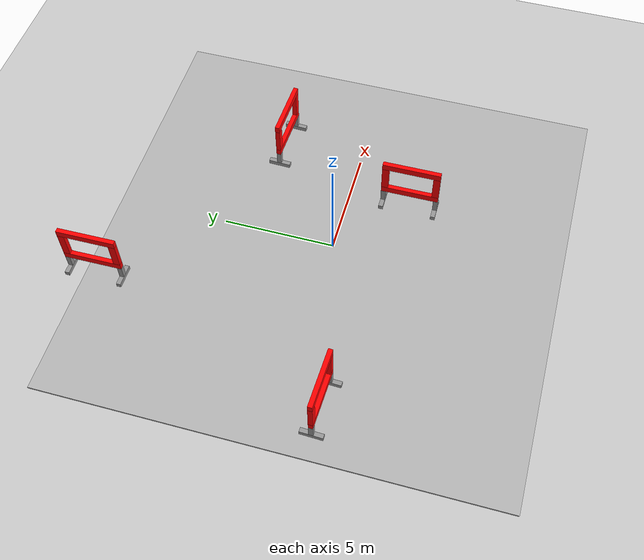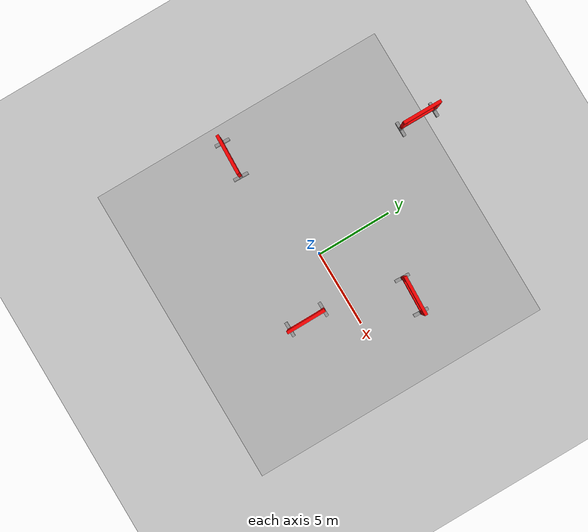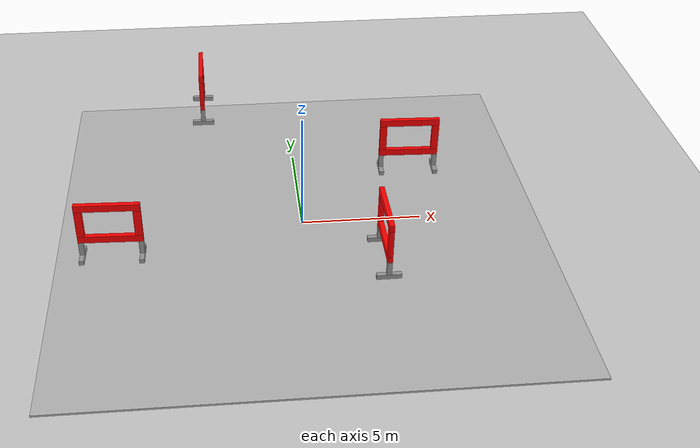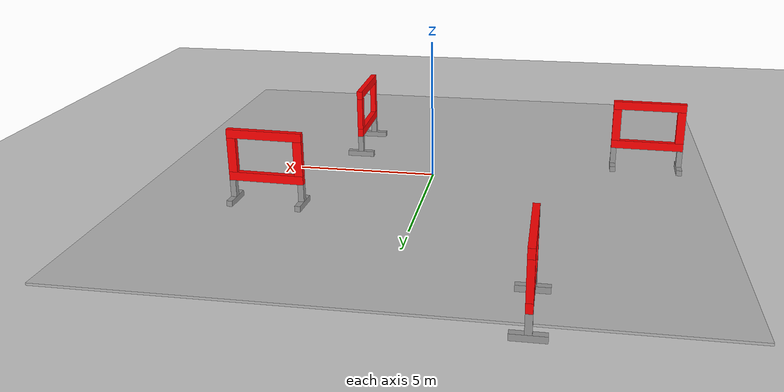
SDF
<sdf version="1.6">
 <world name="default">
  <light name="sun" type="directional">
   <pose>0 0 10 0 -0 0</pose>
   <diffuse>0.8 0.8 0.8 1</diffuse>
   <specular>0.2 0.2 0.2 1</specular>
   <attenuation>
    <range>1000</range>
    <constant>0.9</constant>
    <linear>0.01</linear>
    <quadratic>0.001</quadratic>
   </attenuation>
   <direction>-0.5 0.1 -0.9</direction>
  </light>
  <model name="ground_plane">
   <static>1</static>
   <link name="link">
    <collision name="collision">
     <geometry><plane><normal>0 0 1</normal><size>100 100</size></plane></geometry>
     <surface>
      <contact><collide_bitmask>65535</collide_bitmask></contact>
      <friction><ode><mu>100</mu><mu2>50</mu2></ode></friction>
     </surface>
    </collision>
    <visual name="visual">
     <cast_shadows>0</cast_shadows>
     <geometry><plane><normal>0 0 1</normal><size>100 100</size></plane></geometry>
     <material>
      <script><uri>file://media/materials/scripts/gazebo.material</uri><name>Gazebo/Grey</name></script>
     </material>
    </visual>
   </link>
  </model>
  <gravity>0 0 -9.8</gravity>
  <magnetic_field>6e-06 2.3e-05 -4.2e-05</magnetic_field>
  <atmosphere type="adiabatic"/>
  <physics name="default_physics" default="0" type="ode">
   <max_step_size>0.004</max_step_size>
   <real_time_factor>1</real_time_factor>
   <real_time_update_rate>250</real_time_update_rate>
  </physics>
  <scene><ambient>0.4 0.4 0.4 1</ambient><background>0.7 0.7 0.7 1</background><shadows>1</shadows></scene>
  <spherical_coordinates>
   <surface_model>EARTH_WGS84</surface_model>
   <latitude_deg>0</latitude_deg>
   <longitude_deg>0</longitude_deg>
   <elevation>0</elevation>
   <heading_deg>0</heading_deg>
  </spherical_coordinates>
  <model name="door_2_1.2_0">
   <model name="door">
    <link name="link_0">
     <inertial>
      <mass>1</mass>
      <inertia>
       <ixx>0.166667</ixx>
       <ixy>0</ixy>
       <ixz>0</ixz>
       <iyy>0.166667</iyy>
       <iyz>0</iyz>
       <izz>0.166667</izz>
      </inertia>
     </inertial>
     <pose>-0.195931 0.139969 -0.0875 0 -0 0</pose>
     <visual name="visual">
      <geometry><box><size>0.2 1 0.2</size></box></geometry>
      <material>
       <lighting>1</lighting>
       <script><uri>file://media/materials/scripts/gazebo.material</uri><name>Gazebo/Grey</name></script>
       <shader type="pixel"><normal_map>__default__</normal_map></shader>
       <ambient>0.4 0.4 0.4 1</ambient>
       <diffuse>0.7 0.7 0.7 1</diffuse>
       <specular>0.01 0.01 0.01 1</specular>
       <emissive>0 0 0 1</emissive>
      </material>
     </visual>
     <collision name="collision">
      <geometry><box><size>0.2 1 0.2</size></box></geometry>
      <surface>
       <friction>
        <ode><mu>1</mu><mu2>1</mu2><fdir1>0 0 0</fdir1><slip1>0</slip1><slip2>0</slip2></ode>
        <torsional>
         <coefficient>1</coefficient>
         <patch_radius>0</patch_radius>
         <surface_radius>0</surface_radius>
         <use_patch_radius>1</use_patch_radius>
         <ode><slip>0</slip></ode>
        </torsional>
       </friction>
       <bounce><restitution_coefficient>0</restitution_coefficient><threshold>1e+06</threshold></bounce>
       <contact>
        <collide_without_contact>0</collide_without_contact>
        <collide_without_contact_bitmask>1</collide_without_contact_bitmask>
        <collide_bitmask>1</collide_bitmask>
        <ode>
         <soft_cfm>0</soft_cfm>
         <soft_erp>0.2</soft_erp>
         <kp>1e+13</kp>
         <kd>1</kd>
         <max_vel>0.01</max_vel>
         <min_depth>0</min_depth>
        </ode>
        <bullet>
         <split_impulse>1</split_impulse>
         <split_impulse_penetration_threshold>-0.01</split_impulse_penetration_threshold>
         <soft_cfm>0</soft_cfm>
         <soft_erp>0.2</soft_erp>
         <kp>1e+13</kp>
         <kd>1</kd>
        </bullet>
       </contact>
      </surface>
     </collision>
    </link>
    <link name="link_0_clone">
     <inertial>
      <mass>1</mass>
      <inertia>
       <ixx>0.166667</ixx>
       <ixy>0</ixy>
       <ixz>0</ixz>
       <iyy>0.166667</iyy>
       <iyz>0</iyz>
       <izz>0.166667</izz>
      </inertia>
     </inertial>
     <pose>2.20407 0.139969 -0.0875 0 -0 0</pose>
     <visual name="visual">
      <geometry><box><size>0.2 1 0.2</size></box></geometry>
      <material>
       <lighting>1</lighting>
       <script><uri>file://media/materials/scripts/gazebo.material</uri><name>Gazebo/Grey</name></script>
       <shader type="pixel"><normal_map>__default__</normal_map></shader>
       <ambient>0.4 0.4 0.4 1</ambient>
       <diffuse>0.7 0.7 0.7 1</diffuse>
       <specular>0.01 0.01 0.01 1</specular>
       <emissive>0 0 0 1</emissive>
      </material>
     </visual>
     <collision name="collision">
      <geometry><box><size>0.2 1 0.2</size></box></geometry>
      <surface>
       <friction>
        <ode><mu>1</mu><mu2>1</mu2><fdir1>0 0 0</fdir1><slip1>0</slip1><slip2>0</slip2></ode>
        <torsional>
         <coefficient>1</coefficient>
         <patch_radius>0</patch_radius>
         <surface_radius>0</surface_radius>
         <use_patch_radius>1</use_patch_radius>
         <ode><slip>0</slip></ode>
        </torsional>
       </friction>
       <bounce><restitution_coefficient>0</restitution_coefficient><threshold>1e+06</threshold></bounce>
       <contact>
        <collide_without_contact>0</collide_without_contact>
        <collide_without_contact_bitmask>1</collide_without_contact_bitmask>
        <collide_bitmask>1</collide_bitmask>
        <ode>
         <soft_cfm>0</soft_cfm>
         <soft_erp>0.2</soft_erp>
         <kp>1e+13</kp>
         <kd>1</kd>
         <max_vel>0.01</max_vel>
         <min_depth>0</min_depth>
        </ode>
        <bullet>
         <split_impulse>1</split_impulse>
         <split_impulse_penetration_threshold>-0.01</split_impulse_penetration_threshold>
         <soft_cfm>0</soft_cfm>
         <soft_erp>0.2</soft_erp>
         <kp>1e+13</kp>
         <kd>1</kd>
        </bullet>
       </contact>
      </surface>
     </collision>
    </link>
    <link name="link_1">
     <inertial>
      <mass>1</mass>
      <inertia>
       <ixx>0.166667</ixx>
       <ixy>0</ixy>
       <ixz>0</ixz>
       <iyy>0.166667</iyy>
       <iyz>0</iyz>
       <izz>0.166667</izz>
      </inertia>
     </inertial>
     <pose>-0.195931 0.139969 0.3125 0 -0 0</pose>
     <visual name="visual">
      <geometry><box><size>0.2 0.2 0.6</size></box></geometry>
      <material>
       <lighting>1</lighting>
       <script><uri>file://media/materials/scripts/gazebo.material</uri><name>Gazebo/Grey</name></script>
       <shader type="pixel"><normal_map>__default__</normal_map></shader>
       <ambient>0.4 0.4 0.4 1</ambient>
       <diffuse>0.7 0.7 0.7 1</diffuse>
       <specular>0.01 0.01 0.01 1</specular>
       <emissive>0 0 0 1</emissive>
      </material>
     </visual>
     <collision name="collision">
      <geometry><box><size>0.2 0.2 0.6</size></box></geometry>
      <surface>
       <friction>
        <ode><mu>1</mu><mu2>1</mu2><fdir1>0 0 0</fdir1><slip1>0</slip1><slip2>0</slip2></ode>
        <torsional>
         <coefficient>1</coefficient>
         <patch_radius>0</patch_radius>
         <surface_radius>0</surface_radius>
         <use_patch_radius>1</use_patch_radius>
         <ode><slip>0</slip></ode>
        </torsional>
       </friction>
       <bounce><restitution_coefficient>0</restitution_coefficient><threshold>1e+06</threshold></bounce>
       <contact>
        <collide_without_contact>0</collide_without_contact>
        <collide_without_contact_bitmask>1</collide_without_contact_bitmask>
        <collide_bitmask>1</collide_bitmask>
        <ode>
         <soft_cfm>0</soft_cfm>
         <soft_erp>0.2</soft_erp>
         <kp>1e+13</kp>
         <kd>1</kd>
         <max_vel>0.01</max_vel>
         <min_depth>0</min_depth>
        </ode>
        <bullet>
         <split_impulse>1</split_impulse>
         <split_impulse_penetration_threshold>-0.01</split_impulse_penetration_threshold>
         <soft_cfm>0</soft_cfm>
         <soft_erp>0.2</soft_erp>
         <kp>1e+13</kp>
         <kd>1</kd>
        </bullet>
       </contact>
      </surface>
     </collision>
    </link>
    <link name="link_1_clone">
     <inertial>
      <mass>1</mass>
      <inertia>
       <ixx>0.166667</ixx>
       <ixy>0</ixy>
       <ixz>0</ixz>
       <iyy>0.166667</iyy>
       <iyz>0</iyz>
       <izz>0.166667</izz>
      </inertia>
     </inertial>
     <pose>2.20407 0.139969 0.3125 0 -0 0</pose>
     <visual name="visual">
      <geometry><box><size>0.2 0.2 0.6</size></box></geometry>
      <material>
       <lighting>1</lighting>
       <script><uri>file://media/materials/scripts/gazebo.material</uri><name>Gazebo/Grey</name></script>
       <shader type="pixel"><normal_map>__default__</normal_map></shader>
       <ambient>0.4 0.4 0.4 1</ambient>
       <diffuse>0.7 0.7 0.7 1</diffuse>
       <specular>0.01 0.01 0.01 1</specular>
       <emissive>0 0 0 1</emissive>
      </material>
     </visual>
     <collision name="collision">
      <geometry><box><size>0.2 0.2 0.6</size></box></geometry>
      <surface>
       <friction>
        <ode><mu>1</mu><mu2>1</mu2><fdir1>0 0 0</fdir1><slip1>0</slip1><slip2>0</slip2></ode>
        <torsional>
         <coefficient>1</coefficient>
         <patch_radius>0</patch_radius>
         <surface_radius>0</surface_radius>
         <use_patch_radius>1</use_patch_radius>
         <ode><slip>0</slip></ode>
        </torsional>
       </friction>
       <bounce><restitution_coefficient>0</restitution_coefficient><threshold>1e+06</threshold></bounce>
       <contact>
        <collide_without_contact>0</collide_without_contact>
        <collide_without_contact_bitmask>1</collide_without_contact_bitmask>
        <collide_bitmask>1</collide_bitmask>
        <ode>
         <soft_cfm>0</soft_cfm>
         <soft_erp>0.2</soft_erp>
         <kp>1e+13</kp>
         <kd>1</kd>
         <max_vel>0.01</max_vel>
         <min_depth>0</min_depth>
        </ode>
        <bullet>
         <split_impulse>1</split_impulse>
         <split_impulse_penetration_threshold>-0.01</split_impulse_penetration_threshold>
         <soft_cfm>0</soft_cfm>
         <soft_erp>0.2</soft_erp>
         <kp>1e+13</kp>
         <kd>1</kd>
        </bullet>
       </contact>
      </surface>
     </collision>
    </link>
    <link name="link_2">
     <inertial>
      <mass>1</mass>
      <inertia>
       <ixx>0.166667</ixx>
       <ixy>0</ixy>
       <ixz>0</ixz>
       <iyy>0.166667</iyy>
       <iyz>0</iyz>
       <izz>0.166667</izz>
      </inertia>
     </inertial>
     <pose>1.00407 0.139969 0.7625 0 -0 0</pose>
     <visual name="visual">
      <geometry><box><size>2.6 0.2 0.3</size></box></geometry>
      <material>
       <lighting>1</lighting>
       <script><uri>file://media/materials/scripts/gazebo.material</uri><name>Gazebo/Grey</name></script>
       <shader type="pixel"><normal_map>__default__</normal_map></shader>
       <ambient>1 0 0 1</ambient>
       <diffuse>0.7 0.7 0.7 1</diffuse>
       <specular>0.01 0.01 0.01 1</specular>
       <emissive>0 0 0 1</emissive>
      </material>
     </visual>
     <collision name="collision">
      <geometry><box><size>2.6 0.2 0.3</size></box></geometry>
      <surface>
       <friction>
        <ode><mu>1</mu><mu2>1</mu2><fdir1>0 0 0</fdir1><slip1>0</slip1><slip2>0</slip2></ode>
        <torsional>
         <coefficient>1</coefficient>
         <patch_radius>0</patch_radius>
         <surface_radius>0</surface_radius>
         <use_patch_radius>1</use_patch_radius>
         <ode><slip>0</slip></ode>
        </torsional>
       </friction>
       <bounce><restitution_coefficient>0</restitution_coefficient><threshold>1e+06</threshold></bounce>
       <contact>
        <collide_without_contact>0</collide_without_contact>
        <collide_without_contact_bitmask>1</collide_without_contact_bitmask>
        <collide_bitmask>1</collide_bitmask>
        <ode>
         <soft_cfm>0</soft_cfm>
         <soft_erp>0.2</soft_erp>
         <kp>1e+13</kp>
         <kd>1</kd>
         <max_vel>0.01</max_vel>
         <min_depth>0</min_depth>
        </ode>
        <bullet>
         <split_impulse>1</split_impulse>
         <split_impulse_penetration_threshold>-0.01</split_impulse_penetration_threshold>
         <soft_cfm>0</soft_cfm>
         <soft_erp>0.2</soft_erp>
         <kp>1e+13</kp>
         <kd>1</kd>
        </bullet>
       </contact>
      </surface>
     </collision>
    </link>
    <link name="link_2_clone">
     <inertial>
      <mass>1</mass>
      <inertia>
       <ixx>0.166667</ixx>
       <ixy>0</ixy>
       <ixz>0</ixz>
       <iyy>0.166667</iyy>
       <iyz>0</iyz>
       <izz>0.166667</izz>
      </inertia>
     </inertial>
     <pose>1.00407 0.139969 2.2625 0 -0 0</pose>
     <visual name="visual">
      <geometry><box><size>2.6 0.2 0.3</size></box></geometry>
      <material>
       <lighting>1</lighting>
       <script><uri>file://media/materials/scripts/gazebo.material</uri><name>Gazebo/Grey</name></script>
       <shader type="pixel"><normal_map>__default__</normal_map></shader>
       <ambient>1 0 0 1</ambient>
       <diffuse>0 0 0 1</diffuse>
       <specular>0 0 0 1</specular>
       <emissive>0 0 0 1</emissive>
      </material>
     </visual>
     <collision name="collision">
      <geometry><box><size>2.6 0.2 0.3</size></box></geometry>
      <surface>
       <friction>
        <ode><mu>1</mu><mu2>1</mu2><fdir1>0 0 0</fdir1><slip1>0</slip1><slip2>0</slip2></ode>
        <torsional>
         <coefficient>1</coefficient>
         <patch_radius>0</patch_radius>
         <surface_radius>0</surface_radius>
         <use_patch_radius>1</use_patch_radius>
         <ode><slip>0</slip></ode>
        </torsional>
       </friction>
       <bounce><restitution_coefficient>0</restitution_coefficient><threshold>1e+06</threshold></bounce>
       <contact>
        <collide_without_contact>0</collide_without_contact>
        <collide_without_contact_bitmask>1</collide_without_contact_bitmask>
        <collide_bitmask>1</collide_bitmask>
        <ode>
         <soft_cfm>0</soft_cfm>
         <soft_erp>0.2</soft_erp>
         <kp>1e+13</kp>
         <kd>1</kd>
         <max_vel>0.01</max_vel>
         <min_depth>0</min_depth>
        </ode>
        <bullet>
         <split_impulse>1</split_impulse>
         <split_impulse_penetration_threshold>-0.01</split_impulse_penetration_threshold>
         <soft_cfm>0</soft_cfm>
         <soft_erp>0.2</soft_erp>
         <kp>1e+13</kp>
         <kd>1</kd>
        </bullet>
       </contact>
      </surface>
     </collision>
    </link>
    <link name="link_3">
     <inertial>
      <mass>1</mass>
      <inertia>
       <ixx>0.166667</ixx>
       <ixy>0</ixy>
       <ixz>0</ixz>
       <iyy>0.166667</iyy>
       <iyz>0</iyz>
       <izz>0.166667</izz>
      </inertia>
     </inertial>
     <pose>-0.145931 0.139969 1.5125 0 -0 0</pose>
     <visual name="visual">
      <geometry><box><size>0.3 0.2 1.2</size></box></geometry>
      <material>
       <lighting>1</lighting>
       <script><uri>file://media/materials/scripts/gazebo.material</uri><name>Gazebo/Grey</name></script>
       <shader type="pixel"><normal_map>__default__</normal_map></shader>
       <ambient>1 0 0 1</ambient>
       <diffuse>0.7 0.7 0.7 1</diffuse>
       <specular>0.01 0.01 0.01 1</specular>
       <emissive>0 0 0 1</emissive>
      </material>
     </visual>
     <collision name="collision">
      <geometry><box><size>0.3 0.2 1.2</size></box></geometry>
      <surface>
       <friction>
        <ode><mu>1</mu><mu2>1</mu2><fdir1>0 0 0</fdir1><slip1>0</slip1><slip2>0</slip2></ode>
        <torsional>
         <coefficient>1</coefficient>
         <patch_radius>0</patch_radius>
         <surface_radius>0</surface_radius>
         <use_patch_radius>1</use_patch_radius>
         <ode><slip>0</slip></ode>
        </torsional>
       </friction>
       <bounce><restitution_coefficient>0</restitution_coefficient><threshold>1e+06</threshold></bounce>
       <contact>
        <collide_without_contact>0</collide_without_contact>
        <collide_without_contact_bitmask>1</collide_without_contact_bitmask>
        <collide_bitmask>1</collide_bitmask>
        <ode>
         <soft_cfm>0</soft_cfm>
         <soft_erp>0.2</soft_erp>
         <kp>1e+13</kp>
         <kd>1</kd>
         <max_vel>0.01</max_vel>
         <min_depth>0</min_depth>
        </ode>
        <bullet>
         <split_impulse>1</split_impulse>
         <split_impulse_penetration_threshold>-0.01</split_impulse_penetration_threshold>
         <soft_cfm>0</soft_cfm>
         <soft_erp>0.2</soft_erp>
         <kp>1e+13</kp>
         <kd>1</kd>
        </bullet>
       </contact>
      </surface>
     </collision>
    </link>
    <link name="link_3_clone">
     <inertial>
      <mass>1</mass>
      <inertia>
       <ixx>0.166667</ixx>
       <ixy>0</ixy>
       <ixz>0</ixz>
       <iyy>0.166667</iyy>
       <iyz>0</iyz>
       <izz>0.166667</izz>
      </inertia>
     </inertial>
     <pose>2.15407 0.139969 1.5125 0 -0 0</pose>
     <visual name="visual">
      <geometry><box><size>0.3 0.2 1.2</size></box></geometry>
      <material>
       <lighting>1</lighting>
       <script><uri>file://media/materials/scripts/gazebo.material</uri><name>Gazebo/Grey</name></script>
       <shader type="pixel"><normal_map>__default__</normal_map></shader>
       <ambient>1 0 0 1</ambient>
       <diffuse>0.7 0.7 0.7 1</diffuse>
       <specular>0.01 0.01 0.01 1</specular>
       <emissive>0 0 0 1</emissive>
      </material>
     </visual>
     <collision name="collision">
      <geometry><box><size>0.3 0.2 1.2</size></box></geometry>
      <surface>
       <friction>
        <ode><mu>1</mu><mu2>1</mu2><fdir1>0 0 0</fdir1><slip1>0</slip1><slip2>0</slip2></ode>
        <torsional>
         <coefficient>1</coefficient>
         <patch_radius>0</patch_radius>
         <surface_radius>0</surface_radius>
         <use_patch_radius>1</use_patch_radius>
         <ode><slip>0</slip></ode>
        </torsional>
       </friction>
       <bounce><restitution_coefficient>0</restitution_coefficient><threshold>1e+06</threshold></bounce>
       <contact>
        <collide_without_contact>0</collide_without_contact>
        <collide_without_contact_bitmask>1</collide_without_contact_bitmask>
        <collide_bitmask>1</collide_bitmask>
        <ode>
         <soft_cfm>0</soft_cfm>
         <soft_erp>0.2</soft_erp>
         <kp>1e+13</kp>
         <kd>1</kd>
         <max_vel>0.01</max_vel>
         <min_depth>0</min_depth>
        </ode>
        <bullet>
         <split_impulse>1</split_impulse>
         <split_impulse_penetration_threshold>-0.01</split_impulse_penetration_threshold>
         <soft_cfm>0</soft_cfm>
         <soft_erp>0.2</soft_erp>
         <kp>1e+13</kp>
         <kd>1</kd>
        </bullet>
       </contact>
      </surface>
     </collision>
    </link>
    <joint name="link_0_JOINT_0" type="fixed">
     <parent>link_0</parent>
     <child>link_0_clone</child>
     <physics>
      <ode><limit><cfm>0</cfm><erp>0.2</erp></limit><suspension><cfm>0</cfm><erp>0.2</erp></suspension></ode>
     </physics>
    </joint>
    <joint name="link_0_JOINT_1" type="fixed">
     <parent>link_0</parent>
     <child>link_1</child>
     <physics>
      <ode><limit><cfm>0</cfm><erp>0.2</erp></limit><suspension><cfm>0</cfm><erp>0.2</erp></suspension></ode>
     </physics>
    </joint>
    <joint name="link_0_clone_JOINT_2" type="fixed">
     <parent>link_0_clone</parent>
     <child>link_1_clone</child>
     <physics>
      <ode><limit><cfm>0</cfm><erp>0.2</erp></limit><suspension><cfm>0</cfm><erp>0.2</erp></suspension></ode>
     </physics>
    </joint>
    <joint name="link_1_JOINT_3" type="fixed">
     <parent>link_1</parent>
     <child>link_2</child>
     <physics>
      <ode><limit><cfm>0</cfm><erp>0.2</erp></limit><suspension><cfm>0</cfm><erp>0.2</erp></suspension></ode>
     </physics>
    </joint>
    <joint name="link_2_JOINT_4" type="fixed">
     <parent>link_2</parent>
     <child>link_3</child>
     <physics>
      <ode><limit><cfm>0</cfm><erp>0.2</erp></limit><suspension><cfm>0</cfm><erp>0.2</erp></suspension></ode>
     </physics>
    </joint>
    <joint name="link_2_JOINT_5" type="fixed">
     <parent>link_2</parent>
     <child>link_3_clone</child>
     <physics>
      <ode><limit><cfm>0</cfm><erp>0.2</erp></limit><suspension><cfm>0</cfm><erp>0.2</erp></suspension></ode>
     </physics>
    </joint>
    <joint name="link_2_JOINT_6" type="fixed">
     <parent>link_2</parent>
     <child>link_2_clone</child>
     <physics>
      <ode><limit><cfm>0</cfm><erp>0.2</erp></limit><suspension><cfm>0</cfm><erp>0.2</erp></suspension></ode>
     </physics>
    </joint>
    <static>0</static>
   </model>
   <static>0</static>
   <pose>3.20535 -3.73705 0.237499 -3e-06 4.3e-05 1.57655</pose>
  </model>
  <model name="door_2_1.2_0_clone">
   <model name="door">
    <link name="link_0">
     <inertial>
      <mass>1</mass>
      <inertia>
       <ixx>0.166667</ixx>
       <ixy>0</ixy>
       <ixz>0</ixz>
       <iyy>0.166667</iyy>
       <iyz>0</iyz>
       <izz>0.166667</izz>
      </inertia>
     </inertial>
     <pose>-0.195931 0.139969 -0.0875 0 -0 0</pose>
     <visual name="visual">
      <geometry><box><size>0.2 1 0.2</size></box></geometry>
      <material>
       <lighting>1</lighting>
       <script><uri>file://media/materials/scripts/gazebo.material</uri><name>Gazebo/Grey</name></script>
       <shader type="pixel"><normal_map>__default__</normal_map></shader>
       <ambient>0.4 0.4 0.4 1</ambient>
       <diffuse>0.7 0.7 0.7 1</diffuse>
       <specular>0.01 0.01 0.01 1</specular>
       <emissive>0 0 0 1</emissive>
      </material>
     </visual>
     <collision name="collision">
      <geometry><box><size>0.2 1 0.2</size></box></geometry>
      <surface>
       <friction>
        <ode><mu>1</mu><mu2>1</mu2><fdir1>0 0 0</fdir1><slip1>0</slip1><slip2>0</slip2></ode>
        <torsional>
         <coefficient>1</coefficient>
         <patch_radius>0</patch_radius>
         <surface_radius>0</surface_radius>
         <use_patch_radius>1</use_patch_radius>
         <ode><slip>0</slip></ode>
        </torsional>
       </friction>
       <bounce><restitution_coefficient>0</restitution_coefficient><threshold>1e+06</threshold></bounce>
       <contact>
        <collide_without_contact>0</collide_without_contact>
        <collide_without_contact_bitmask>1</collide_without_contact_bitmask>
        <collide_bitmask>1</collide_bitmask>
        <ode>
         <soft_cfm>0</soft_cfm>
         <soft_erp>0.2</soft_erp>
         <kp>1e+13</kp>
         <kd>1</kd>
         <max_vel>0.01</max_vel>
         <min_depth>0</min_depth>
        </ode>
        <bullet>
         <split_impulse>1</split_impulse>
         <split_impulse_penetration_threshold>-0.01</split_impulse_penetration_threshold>
         <soft_cfm>0</soft_cfm>
         <soft_erp>0.2</soft_erp>
         <kp>1e+13</kp>
         <kd>1</kd>
        </bullet>
       </contact>
      </surface>
     </collision>
    </link>
    <link name="link_0_clone">
     <inertial>
      <mass>1</mass>
      <inertia>
       <ixx>0.166667</ixx>
       <ixy>0</ixy>
       <ixz>0</ixz>
       <iyy>0.166667</iyy>
       <iyz>0</iyz>
       <izz>0.166667</izz>
      </inertia>
     </inertial>
     <pose>2.20407 0.139969 -0.0875 0 -0 0</pose>
     <visual name="visual">
      <geometry><box><size>0.2 1 0.2</size></box></geometry>
      <material>
       <lighting>1</lighting>
       <script><uri>file://media/materials/scripts/gazebo.material</uri><name>Gazebo/Grey</name></script>
       <shader type="pixel"><normal_map>__default__</normal_map></shader>
       <ambient>0.4 0.4 0.4 1</ambient>
       <diffuse>0.7 0.7 0.7 1</diffuse>
       <specular>0.01 0.01 0.01 1</specular>
       <emissive>0 0 0 1</emissive>
      </material>
     </visual>
     <collision name="collision">
      <geometry><box><size>0.2 1 0.2</size></box></geometry>
      <surface>
       <friction>
        <ode><mu>1</mu><mu2>1</mu2><fdir1>0 0 0</fdir1><slip1>0</slip1><slip2>0</slip2></ode>
        <torsional>
         <coefficient>1</coefficient>
         <patch_radius>0</patch_radius>
         <surface_radius>0</surface_radius>
         <use_patch_radius>1</use_patch_radius>
         <ode><slip>0</slip></ode>
        </torsional>
       </friction>
       <bounce><restitution_coefficient>0</restitution_coefficient><threshold>1e+06</threshold></bounce>
       <contact>
        <collide_without_contact>0</collide_without_contact>
        <collide_without_contact_bitmask>1</collide_without_contact_bitmask>
        <collide_bitmask>1</collide_bitmask>
        <ode>
         <soft_cfm>0</soft_cfm>
         <soft_erp>0.2</soft_erp>
         <kp>1e+13</kp>
         <kd>1</kd>
         <max_vel>0.01</max_vel>
         <min_depth>0</min_depth>
        </ode>
        <bullet>
         <split_impulse>1</split_impulse>
         <split_impulse_penetration_threshold>-0.01</split_impulse_penetration_threshold>
         <soft_cfm>0</soft_cfm>
         <soft_erp>0.2</soft_erp>
         <kp>1e+13</kp>
         <kd>1</kd>
        </bullet>
       </contact>
      </surface>
     </collision>
    </link>
    <link name="link_1">
     <inertial>
      <mass>1</mass>
      <inertia>
       <ixx>0.166667</ixx>
       <ixy>0</ixy>
       <ixz>0</ixz>
       <iyy>0.166667</iyy>
       <iyz>0</iyz>
       <izz>0.166667</izz>
      </inertia>
     </inertial>
     <pose>-0.195931 0.139969 0.3125 0 -0 0</pose>
     <visual name="visual">
      <geometry><box><size>0.2 0.2 0.6</size></box></geometry>
      <material>
       <lighting>1</lighting>
       <script><uri>file://media/materials/scripts/gazebo.material</uri><name>Gazebo/Grey</name></script>
       <shader type="pixel"><normal_map>__default__</normal_map></shader>
       <ambient>0.4 0.4 0.4 1</ambient>
       <diffuse>0.7 0.7 0.7 1</diffuse>
       <specular>0.01 0.01 0.01 1</specular>
       <emissive>0 0 0 1</emissive>
      </material>
     </visual>
     <collision name="collision">
      <geometry><box><size>0.2 0.2 0.6</size></box></geometry>
      <surface>
       <friction>
        <ode><mu>1</mu><mu2>1</mu2><fdir1>0 0 0</fdir1><slip1>0</slip1><slip2>0</slip2></ode>
        <torsional>
         <coefficient>1</coefficient>
         <patch_radius>0</patch_radius>
         <surface_radius>0</surface_radius>
         <use_patch_radius>1</use_patch_radius>
         <ode><slip>0</slip></ode>
        </torsional>
       </friction>
       <bounce><restitution_coefficient>0</restitution_coefficient><threshold>1e+06</threshold></bounce>
       <contact>
        <collide_without_contact>0</collide_without_contact>
        <collide_without_contact_bitmask>1</collide_without_contact_bitmask>
        <collide_bitmask>1</collide_bitmask>
        <ode>
         <soft_cfm>0</soft_cfm>
         <soft_erp>0.2</soft_erp>
         <kp>1e+13</kp>
         <kd>1</kd>
         <max_vel>0.01</max_vel>
         <min_depth>0</min_depth>
        </ode>
        <bullet>
         <split_impulse>1</split_impulse>
         <split_impulse_penetration_threshold>-0.01</split_impulse_penetration_threshold>
         <soft_cfm>0</soft_cfm>
         <soft_erp>0.2</soft_erp>
         <kp>1e+13</kp>
         <kd>1</kd>
        </bullet>
       </contact>
      </surface>
     </collision>
    </link>
    <link name="link_1_clone">
     <inertial>
      <mass>1</mass>
      <inertia>
       <ixx>0.166667</ixx>
       <ixy>0</ixy>
       <ixz>0</ixz>
       <iyy>0.166667</iyy>
       <iyz>0</iyz>
       <izz>0.166667</izz>
      </inertia>
     </inertial>
     <pose>2.20407 0.139969 0.3125 0 -0 0</pose>
     <visual name="visual">
      <geometry><box><size>0.2 0.2 0.6</size></box></geometry>
      <material>
       <lighting>1</lighting>
       <script><uri>file://media/materials/scripts/gazebo.material</uri><name>Gazebo/Grey</name></script>
       <shader type="pixel"><normal_map>__default__</normal_map></shader>
       <ambient>0.4 0.4 0.4 1</ambient>
       <diffuse>0.7 0.7 0.7 1</diffuse>
       <specular>0.01 0.01 0.01 1</specular>
       <emissive>0 0 0 1</emissive>
      </material>
     </visual>
     <collision name="collision">
      <geometry><box><size>0.2 0.2 0.6</size></box></geometry>
      <surface>
       <friction>
        <ode><mu>1</mu><mu2>1</mu2><fdir1>0 0 0</fdir1><slip1>0</slip1><slip2>0</slip2></ode>
        <torsional>
         <coefficient>1</coefficient>
         <patch_radius>0</patch_radius>
         <surface_radius>0</surface_radius>
         <use_patch_radius>1</use_patch_radius>
         <ode><slip>0</slip></ode>
        </torsional>
       </friction>
       <bounce><restitution_coefficient>0</restitution_coefficient><threshold>1e+06</threshold></bounce>
       <contact>
        <collide_without_contact>0</collide_without_contact>
        <collide_without_contact_bitmask>1</collide_without_contact_bitmask>
        <collide_bitmask>1</collide_bitmask>
        <ode>
         <soft_cfm>0</soft_cfm>
         <soft_erp>0.2</soft_erp>
         <kp>1e+13</kp>
         <kd>1</kd>
         <max_vel>0.01</max_vel>
         <min_depth>0</min_depth>
        </ode>
        <bullet>
         <split_impulse>1</split_impulse>
         <split_impulse_penetration_threshold>-0.01</split_impulse_penetration_threshold>
         <soft_cfm>0</soft_cfm>
         <soft_erp>0.2</soft_erp>
         <kp>1e+13</kp>
         <kd>1</kd>
        </bullet>
       </contact>
      </surface>
     </collision>
    </link>
    <link name="link_2">
     <inertial>
      <mass>1</mass>
      <inertia>
       <ixx>0.166667</ixx>
       <ixy>0</ixy>
       <ixz>0</ixz>
       <iyy>0.166667</iyy>
       <iyz>0</iyz>
       <izz>0.166667</izz>
      </inertia>
     </inertial>
     <pose>1.00407 0.139969 0.7625 0 -0 0</pose>
     <visual name="visual">
      <geometry><box><size>2.6 0.2 0.3</size></box></geometry>
      <material>
       <lighting>1</lighting>
       <script><uri>file://media/materials/scripts/gazebo.material</uri><name>Gazebo/Grey</name></script>
       <shader type="pixel"><normal_map>__default__</normal_map></shader>
       <ambient>1 0 0 1</ambient>
       <diffuse>0.7 0.7 0.7 1</diffuse>
       <specular>0.01 0.01 0.01 1</specular>
       <emissive>0 0 0 1</emissive>
      </material>
     </visual>
     <collision name="collision">
      <geometry><box><size>2.6 0.2 0.3</size></box></geometry>
      <surface>
       <friction>
        <ode><mu>1</mu><mu2>1</mu2><fdir1>0 0 0</fdir1><slip1>0</slip1><slip2>0</slip2></ode>
        <torsional>
         <coefficient>1</coefficient>
         <patch_radius>0</patch_radius>
         <surface_radius>0</surface_radius>
         <use_patch_radius>1</use_patch_radius>
         <ode><slip>0</slip></ode>
        </torsional>
       </friction>
       <bounce><restitution_coefficient>0</restitution_coefficient><threshold>1e+06</threshold></bounce>
       <contact>
        <collide_without_contact>0</collide_without_contact>
        <collide_without_contact_bitmask>1</collide_without_contact_bitmask>
        <collide_bitmask>1</collide_bitmask>
        <ode>
         <soft_cfm>0</soft_cfm>
         <soft_erp>0.2</soft_erp>
         <kp>1e+13</kp>
         <kd>1</kd>
         <max_vel>0.01</max_vel>
         <min_depth>0</min_depth>
        </ode>
        <bullet>
         <split_impulse>1</split_impulse>
         <split_impulse_penetration_threshold>-0.01</split_impulse_penetration_threshold>
         <soft_cfm>0</soft_cfm>
         <soft_erp>0.2</soft_erp>
         <kp>1e+13</kp>
         <kd>1</kd>
        </bullet>
       </contact>
      </surface>
     </collision>
    </link>
    <link name="link_2_clone">
     <inertial>
      <mass>1</mass>
      <inertia>
       <ixx>0.166667</ixx>
       <ixy>0</ixy>
       <ixz>0</ixz>
       <iyy>0.166667</iyy>
       <iyz>0</iyz>
       <izz>0.166667</izz>
      </inertia>
     </inertial>
     <pose>1.00407 0.139969 2.2625 0 -0 0</pose>
     <visual name="visual">
      <geometry><box><size>2.6 0.2 0.3</size></box></geometry>
      <material>
       <lighting>1</lighting>
       <script><uri>file://media/materials/scripts/gazebo.material</uri><name>Gazebo/Grey</name></script>
       <shader type="pixel"><normal_map>__default__</normal_map></shader>
       <ambient>1 0 0 1</ambient>
       <diffuse>0 0 0 1</diffuse>
       <specular>0 0 0 1</specular>
       <emissive>0 0 0 1</emissive>
      </material>
     </visual>
     <collision name="collision">
      <geometry><box><size>2.6 0.2 0.3</size></box></geometry>
      <surface>
       <friction>
        <ode><mu>1</mu><mu2>1</mu2><fdir1>0 0 0</fdir1><slip1>0</slip1><slip2>0</slip2></ode>
        <torsional>
         <coefficient>1</coefficient>
         <patch_radius>0</patch_radius>
         <surface_radius>0</surface_radius>
         <use_patch_radius>1</use_patch_radius>
         <ode><slip>0</slip></ode>
        </torsional>
       </friction>
       <bounce><restitution_coefficient>0</restitution_coefficient><threshold>1e+06</threshold></bounce>
       <contact>
        <collide_without_contact>0</collide_without_contact>
        <collide_without_contact_bitmask>1</collide_without_contact_bitmask>
        <collide_bitmask>1</collide_bitmask>
        <ode>
         <soft_cfm>0</soft_cfm>
         <soft_erp>0.2</soft_erp>
         <kp>1e+13</kp>
         <kd>1</kd>
         <max_vel>0.01</max_vel>
         <min_depth>0</min_depth>
        </ode>
        <bullet>
         <split_impulse>1</split_impulse>
         <split_impulse_penetration_threshold>-0.01</split_impulse_penetration_threshold>
         <soft_cfm>0</soft_cfm>
         <soft_erp>0.2</soft_erp>
         <kp>1e+13</kp>
         <kd>1</kd>
        </bullet>
       </contact>
      </surface>
     </collision>
    </link>
    <link name="link_3">
     <inertial>
      <mass>1</mass>
      <inertia>
       <ixx>0.166667</ixx>
       <ixy>0</ixy>
       <ixz>0</ixz>
       <iyy>0.166667</iyy>
       <iyz>0</iyz>
       <izz>0.166667</izz>
      </inertia>
     </inertial>
     <pose>-0.145931 0.139969 1.5125 0 -0 0</pose>
     <visual name="visual">
      <geometry><box><size>0.3 0.2 1.2</size></box></geometry>
      <material>
       <lighting>1</lighting>
       <script><uri>file://media/materials/scripts/gazebo.material</uri><name>Gazebo/Grey</name></script>
       <shader type="pixel"><normal_map>__default__</normal_map></shader>
       <ambient>1 0 0 1</ambient>
       <diffuse>0.7 0.7 0.7 1</diffuse>
       <specular>0.01 0.01 0.01 1</specular>
       <emissive>0 0 0 1</emissive>
      </material>
     </visual>
     <collision name="collision">
      <geometry><box><size>0.3 0.2 1.2</size></box></geometry>
      <surface>
       <friction>
        <ode><mu>1</mu><mu2>1</mu2><fdir1>0 0 0</fdir1><slip1>0</slip1><slip2>0</slip2></ode>
        <torsional>
         <coefficient>1</coefficient>
         <patch_radius>0</patch_radius>
         <surface_radius>0</surface_radius>
         <use_patch_radius>1</use_patch_radius>
         <ode><slip>0</slip></ode>
        </torsional>
       </friction>
       <bounce><restitution_coefficient>0</restitution_coefficient><threshold>1e+06</threshold></bounce>
       <contact>
        <collide_without_contact>0</collide_without_contact>
        <collide_without_contact_bitmask>1</collide_without_contact_bitmask>
        <collide_bitmask>1</collide_bitmask>
        <ode>
         <soft_cfm>0</soft_cfm>
         <soft_erp>0.2</soft_erp>
         <kp>1e+13</kp>
         <kd>1</kd>
         <max_vel>0.01</max_vel>
         <min_depth>0</min_depth>
        </ode>
        <bullet>
         <split_impulse>1</split_impulse>
         <split_impulse_penetration_threshold>-0.01</split_impulse_penetration_threshold>
         <soft_cfm>0</soft_cfm>
         <soft_erp>0.2</soft_erp>
         <kp>1e+13</kp>
         <kd>1</kd>
        </bullet>
       </contact>
      </surface>
     </collision>
    </link>
    <link name="link_3_clone">
     <inertial>
      <mass>1</mass>
      <inertia>
       <ixx>0.166667</ixx>
       <ixy>0</ixy>
       <ixz>0</ixz>
       <iyy>0.166667</iyy>
       <iyz>0</iyz>
       <izz>0.166667</izz>
      </inertia>
     </inertial>
     <pose>2.15407 0.139969 1.5125 0 -0 0</pose>
     <visual name="visual">
      <geometry><box><size>0.3 0.2 1.2</size></box></geometry>
      <material>
       <lighting>1</lighting>
       <script><uri>file://media/materials/scripts/gazebo.material</uri><name>Gazebo/Grey</name></script>
       <shader type="pixel"><normal_map>__default__</normal_map></shader>
       <ambient>1 0 0 1</ambient>
       <diffuse>0.7 0.7 0.7 1</diffuse>
       <specular>0.01 0.01 0.01 1</specular>
       <emissive>0 0 0 1</emissive>
      </material>
     </visual>
     <collision name="collision">
      <geometry><box><size>0.3 0.2 1.2</size></box></geometry>
      <surface>
       <friction>
        <ode><mu>1</mu><mu2>1</mu2><fdir1>0 0 0</fdir1><slip1>0</slip1><slip2>0</slip2></ode>
        <torsional>
         <coefficient>1</coefficient>
         <patch_radius>0</patch_radius>
         <surface_radius>0</surface_radius>
         <use_patch_radius>1</use_patch_radius>
         <ode><slip>0</slip></ode>
        </torsional>
       </friction>
       <bounce><restitution_coefficient>0</restitution_coefficient><threshold>1e+06</threshold></bounce>
       <contact>
        <collide_without_contact>0</collide_without_contact>
        <collide_without_contact_bitmask>1</collide_without_contact_bitmask>
        <collide_bitmask>1</collide_bitmask>
        <ode>
         <soft_cfm>0</soft_cfm>
         <soft_erp>0.2</soft_erp>
         <kp>1e+13</kp>
         <kd>1</kd>
         <max_vel>0.01</max_vel>
         <min_depth>0</min_depth>
        </ode>
        <bullet>
         <split_impulse>1</split_impulse>
         <split_impulse_penetration_threshold>-0.01</split_impulse_penetration_threshold>
         <soft_cfm>0</soft_cfm>
         <soft_erp>0.2</soft_erp>
         <kp>1e+13</kp>
         <kd>1</kd>
        </bullet>
       </contact>
      </surface>
     </collision>
    </link>
    <joint name="link_0_JOINT_0" type="fixed">
     <parent>link_0</parent>
     <child>link_0_clone</child>
     <physics>
      <ode><limit><cfm>0</cfm><erp>0.2</erp></limit><suspension><cfm>0</cfm><erp>0.2</erp></suspension></ode>
     </physics>
    </joint>
    <joint name="link_0_JOINT_1" type="fixed">
     <parent>link_0</parent>
     <child>link_1</child>
     <physics>
      <ode><limit><cfm>0</cfm><erp>0.2</erp></limit><suspension><cfm>0</cfm><erp>0.2</erp></suspension></ode>
     </physics>
    </joint>
    <joint name="link_0_clone_JOINT_2" type="fixed">
     <parent>link_0_clone</parent>
     <child>link_1_clone</child>
     <physics>
      <ode><limit><cfm>0</cfm><erp>0.2</erp></limit><suspension><cfm>0</cfm><erp>0.2</erp></suspension></ode>
     </physics>
    </joint>
    <joint name="link_1_JOINT_3" type="fixed">
     <parent>link_1</parent>
     <child>link_2</child>
     <physics>
      <ode><limit><cfm>0</cfm><erp>0.2</erp></limit><suspension><cfm>0</cfm><erp>0.2</erp></suspension></ode>
     </physics>
    </joint>
    <joint name="link_2_JOINT_4" type="fixed">
     <parent>link_2</parent>
     <child>link_3</child>
     <physics>
      <ode><limit><cfm>0</cfm><erp>0.2</erp></limit><suspension><cfm>0</cfm><erp>0.2</erp></suspension></ode>
     </physics>
    </joint>
    <joint name="link_2_JOINT_5" type="fixed">
     <parent>link_2</parent>
     <child>link_3_clone</child>
     <physics>
      <ode><limit><cfm>0</cfm><erp>0.2</erp></limit><suspension><cfm>0</cfm><erp>0.2</erp></suspension></ode>
     </physics>
    </joint>
    <joint name="link_2_JOINT_6" type="fixed">
     <parent>link_2</parent>
     <child>link_2_clone</child>
     <physics>
      <ode><limit><cfm>0</cfm><erp>0.2</erp></limit><suspension><cfm>0</cfm><erp>0.2</erp></suspension></ode>
     </physics>
    </joint>
    <static>0</static>
   </model>
   <static>0</static>
   <pose>-3.93256 8.48576 0.235454 -1e-06 0.020905 1.56963</pose>
  </model>
  <model name="door_2_1.2_0_clone_0">
   <model name="door">
    <link name="link_0">
     <inertial>
      <mass>1</mass>
      <inertia>
       <ixx>0.166667</ixx>
       <ixy>0</ixy>
       <ixz>0</ixz>
       <iyy>0.166667</iyy>
       <iyz>0</iyz>
       <izz>0.166667</izz>
      </inertia>
     </inertial>
     <pose>-0.195931 0.139969 -0.0875 0 -0 0</pose>
     <visual name="visual">
      <geometry><box><size>0.2 1 0.2</size></box></geometry>
      <material>
       <lighting>1</lighting>
       <script><uri>file://media/materials/scripts/gazebo.material</uri><name>Gazebo/Grey</name></script>
       <shader type="pixel"><normal_map>__default__</normal_map></shader>
       <ambient>0.4 0.4 0.4 1</ambient>
       <diffuse>0.7 0.7 0.7 1</diffuse>
       <specular>0.01 0.01 0.01 1</specular>
       <emissive>0 0 0 1</emissive>
      </material>
     </visual>
     <collision name="collision">
      <geometry><box><size>0.2 1 0.2</size></box></geometry>
      <surface>
       <friction>
        <ode><mu>1</mu><mu2>1</mu2><fdir1>0 0 0</fdir1><slip1>0</slip1><slip2>0</slip2></ode>
        <torsional>
         <coefficient>1</coefficient>
         <patch_radius>0</patch_radius>
         <surface_radius>0</surface_radius>
         <use_patch_radius>1</use_patch_radius>
         <ode><slip>0</slip></ode>
        </torsional>
       </friction>
       <bounce><restitution_coefficient>0</restitution_coefficient><threshold>1e+06</threshold></bounce>
       <contact>
        <collide_without_contact>0</collide_without_contact>
        <collide_without_contact_bitmask>1</collide_without_contact_bitmask>
        <collide_bitmask>1</collide_bitmask>
        <ode>
         <soft_cfm>0</soft_cfm>
         <soft_erp>0.2</soft_erp>
         <kp>1e+13</kp>
         <kd>1</kd>
         <max_vel>0.01</max_vel>
         <min_depth>0</min_depth>
        </ode>
        <bullet>
         <split_impulse>1</split_impulse>
         <split_impulse_penetration_threshold>-0.01</split_impulse_penetration_threshold>
         <soft_cfm>0</soft_cfm>
         <soft_erp>0.2</soft_erp>
         <kp>1e+13</kp>
         <kd>1</kd>
        </bullet>
       </contact>
      </surface>
     </collision>
    </link>
    <link name="link_0_clone">
     <inertial>
      <mass>1</mass>
      <inertia>
       <ixx>0.166667</ixx>
       <ixy>0</ixy>
       <ixz>0</ixz>
       <iyy>0.166667</iyy>
       <iyz>0</iyz>
       <izz>0.166667</izz>
      </inertia>
     </inertial>
     <pose>2.20407 0.139969 -0.0875 0 -0 0</pose>
     <visual name="visual">
      <geometry><box><size>0.2 1 0.2</size></box></geometry>
      <material>
       <lighting>1</lighting>
       <script><uri>file://media/materials/scripts/gazebo.material</uri><name>Gazebo/Grey</name></script>
       <shader type="pixel"><normal_map>__default__</normal_map></shader>
       <ambient>0.4 0.4 0.4 1</ambient>
       <diffuse>0.7 0.7 0.7 1</diffuse>
       <specular>0.01 0.01 0.01 1</specular>
       <emissive>0 0 0 1</emissive>
      </material>
     </visual>
     <collision name="collision">
      <geometry><box><size>0.2 1 0.2</size></box></geometry>
      <surface>
       <friction>
        <ode><mu>1</mu><mu2>1</mu2><fdir1>0 0 0</fdir1><slip1>0</slip1><slip2>0</slip2></ode>
        <torsional>
         <coefficient>1</coefficient>
         <patch_radius>0</patch_radius>
         <surface_radius>0</surface_radius>
         <use_patch_radius>1</use_patch_radius>
         <ode><slip>0</slip></ode>
        </torsional>
       </friction>
       <bounce><restitution_coefficient>0</restitution_coefficient><threshold>1e+06</threshold></bounce>
       <contact>
        <collide_without_contact>0</collide_without_contact>
        <collide_without_contact_bitmask>1</collide_without_contact_bitmask>
        <collide_bitmask>1</collide_bitmask>
        <ode>
         <soft_cfm>0</soft_cfm>
         <soft_erp>0.2</soft_erp>
         <kp>1e+13</kp>
         <kd>1</kd>
         <max_vel>0.01</max_vel>
         <min_depth>0</min_depth>
        </ode>
        <bullet>
         <split_impulse>1</split_impulse>
         <split_impulse_penetration_threshold>-0.01</split_impulse_penetration_threshold>
         <soft_cfm>0</soft_cfm>
         <soft_erp>0.2</soft_erp>
         <kp>1e+13</kp>
         <kd>1</kd>
        </bullet>
       </contact>
      </surface>
     </collision>
    </link>
    <link name="link_1">
     <inertial>
      <mass>1</mass>
      <inertia>
       <ixx>0.166667</ixx>
       <ixy>0</ixy>
       <ixz>0</ixz>
       <iyy>0.166667</iyy>
       <iyz>0</iyz>
       <izz>0.166667</izz>
      </inertia>
     </inertial>
     <pose>-0.195931 0.139969 0.3125 0 -0 0</pose>
     <visual name="visual">
      <geometry><box><size>0.2 0.2 0.6</size></box></geometry>
      <material>
       <lighting>1</lighting>
       <script><uri>file://media/materials/scripts/gazebo.material</uri><name>Gazebo/Grey</name></script>
       <shader type="pixel"><normal_map>__default__</normal_map></shader>
       <ambient>0.4 0.4 0.4 1</ambient>
       <diffuse>0.7 0.7 0.7 1</diffuse>
       <specular>0.01 0.01 0.01 1</specular>
       <emissive>0 0 0 1</emissive>
      </material>
     </visual>
     <collision name="collision">
      <geometry><box><size>0.2 0.2 0.6</size></box></geometry>
      <surface>
       <friction>
        <ode><mu>1</mu><mu2>1</mu2><fdir1>0 0 0</fdir1><slip1>0</slip1><slip2>0</slip2></ode>
        <torsional>
         <coefficient>1</coefficient>
         <patch_radius>0</patch_radius>
         <surface_radius>0</surface_radius>
         <use_patch_radius>1</use_patch_radius>
         <ode><slip>0</slip></ode>
        </torsional>
       </friction>
       <bounce><restitution_coefficient>0</restitution_coefficient><threshold>1e+06</threshold></bounce>
       <contact>
        <collide_without_contact>0</collide_without_contact>
        <collide_without_contact_bitmask>1</collide_without_contact_bitmask>
        <collide_bitmask>1</collide_bitmask>
        <ode>
         <soft_cfm>0</soft_cfm>
         <soft_erp>0.2</soft_erp>
         <kp>1e+13</kp>
         <kd>1</kd>
         <max_vel>0.01</max_vel>
         <min_depth>0</min_depth>
        </ode>
        <bullet>
         <split_impulse>1</split_impulse>
         <split_impulse_penetration_threshold>-0.01</split_impulse_penetration_threshold>
         <soft_cfm>0</soft_cfm>
         <soft_erp>0.2</soft_erp>
         <kp>1e+13</kp>
         <kd>1</kd>
        </bullet>
       </contact>
      </surface>
     </collision>
    </link>
    <link name="link_1_clone">
     <inertial>
      <mass>1</mass>
      <inertia>
       <ixx>0.166667</ixx>
       <ixy>0</ixy>
       <ixz>0</ixz>
       <iyy>0.166667</iyy>
       <iyz>0</iyz>
       <izz>0.166667</izz>
      </inertia>
     </inertial>
     <pose>2.20407 0.139969 0.3125 0 -0 0</pose>
     <visual name="visual">
      <geometry><box><size>0.2 0.2 0.6</size></box></geometry>
      <material>
       <lighting>1</lighting>
       <script><uri>file://media/materials/scripts/gazebo.material</uri><name>Gazebo/Grey</name></script>
       <shader type="pixel"><normal_map>__default__</normal_map></shader>
       <ambient>0.4 0.4 0.4 1</ambient>
       <diffuse>0.7 0.7 0.7 1</diffuse>
       <specular>0.01 0.01 0.01 1</specular>
       <emissive>0 0 0 1</emissive>
      </material>
     </visual>
     <collision name="collision">
      <geometry><box><size>0.2 0.2 0.6</size></box></geometry>
      <surface>
       <friction>
        <ode><mu>1</mu><mu2>1</mu2><fdir1>0 0 0</fdir1><slip1>0</slip1><slip2>0</slip2></ode>
        <torsional>
         <coefficient>1</coefficient>
         <patch_radius>0</patch_radius>
         <surface_radius>0</surface_radius>
         <use_patch_radius>1</use_patch_radius>
         <ode><slip>0</slip></ode>
        </torsional>
       </friction>
       <bounce><restitution_coefficient>0</restitution_coefficient><threshold>1e+06</threshold></bounce>
       <contact>
        <collide_without_contact>0</collide_without_contact>
        <collide_without_contact_bitmask>1</collide_without_contact_bitmask>
        <collide_bitmask>1</collide_bitmask>
        <ode>
         <soft_cfm>0</soft_cfm>
         <soft_erp>0.2</soft_erp>
         <kp>1e+13</kp>
         <kd>1</kd>
         <max_vel>0.01</max_vel>
         <min_depth>0</min_depth>
        </ode>
        <bullet>
         <split_impulse>1</split_impulse>
         <split_impulse_penetration_threshold>-0.01</split_impulse_penetration_threshold>
         <soft_cfm>0</soft_cfm>
         <soft_erp>0.2</soft_erp>
         <kp>1e+13</kp>
         <kd>1</kd>
        </bullet>
       </contact>
      </surface>
     </collision>
    </link>
    <link name="link_2">
     <inertial>
      <mass>1</mass>
      <inertia>
       <ixx>0.166667</ixx>
       <ixy>0</ixy>
       <ixz>0</ixz>
       <iyy>0.166667</iyy>
       <iyz>0</iyz>
       <izz>0.166667</izz>
      </inertia>
     </inertial>
     <pose>1.00407 0.139969 0.7625 0 -0 0</pose>
     <visual name="visual">
      <geometry><box><size>2.6 0.2 0.3</size></box></geometry>
      <material>
       <lighting>1</lighting>
       <script><uri>file://media/materials/scripts/gazebo.material</uri><name>Gazebo/Grey</name></script>
       <shader type="pixel"><normal_map>__default__</normal_map></shader>
       <ambient>1 0 0 1</ambient>
       <diffuse>0.7 0.7 0.7 1</diffuse>
       <specular>0.01 0.01 0.01 1</specular>
       <emissive>0 0 0 1</emissive>
      </material>
     </visual>
     <collision name="collision">
      <geometry><box><size>2.6 0.2 0.3</size></box></geometry>
      <surface>
       <friction>
        <ode><mu>1</mu><mu2>1</mu2><fdir1>0 0 0</fdir1><slip1>0</slip1><slip2>0</slip2></ode>
        <torsional>
         <coefficient>1</coefficient>
         <patch_radius>0</patch_radius>
         <surface_radius>0</surface_radius>
         <use_patch_radius>1</use_patch_radius>
         <ode><slip>0</slip></ode>
        </torsional>
       </friction>
       <bounce><restitution_coefficient>0</restitution_coefficient><threshold>1e+06</threshold></bounce>
       <contact>
        <collide_without_contact>0</collide_without_contact>
        <collide_without_contact_bitmask>1</collide_without_contact_bitmask>
        <collide_bitmask>1</collide_bitmask>
        <ode>
         <soft_cfm>0</soft_cfm>
         <soft_erp>0.2</soft_erp>
         <kp>1e+13</kp>
         <kd>1</kd>
         <max_vel>0.01</max_vel>
         <min_depth>0</min_depth>
        </ode>
        <bullet>
         <split_impulse>1</split_impulse>
         <split_impulse_penetration_threshold>-0.01</split_impulse_penetration_threshold>
         <soft_cfm>0</soft_cfm>
         <soft_erp>0.2</soft_erp>
         <kp>1e+13</kp>
         <kd>1</kd>
        </bullet>
       </contact>
      </surface>
     </collision>
    </link>
    <link name="link_2_clone">
     <inertial>
      <mass>1</mass>
      <inertia>
       <ixx>0.166667</ixx>
       <ixy>0</ixy>
       <ixz>0</ixz>
       <iyy>0.166667</iyy>
       <iyz>0</iyz>
       <izz>0.166667</izz>
      </inertia>
     </inertial>
     <pose>1.00407 0.139969 2.2625 0 -0 0</pose>
     <visual name="visual">
      <geometry><box><size>2.6 0.2 0.3</size></box></geometry>
      <material>
       <lighting>1</lighting>
       <script><uri>file://media/materials/scripts/gazebo.material</uri><name>Gazebo/Grey</name></script>
       <shader type="pixel"><normal_map>__default__</normal_map></shader>
       <ambient>1 0 0 1</ambient>
       <diffuse>0 0 0 1</diffuse>
       <specular>0 0 0 1</specular>
       <emissive>0 0 0 1</emissive>
      </material>
     </visual>
     <collision name="collision">
      <geometry><box><size>2.6 0.2 0.3</size></box></geometry>
      <surface>
       <friction>
        <ode><mu>1</mu><mu2>1</mu2><fdir1>0 0 0</fdir1><slip1>0</slip1><slip2>0</slip2></ode>
        <torsional>
         <coefficient>1</coefficient>
         <patch_radius>0</patch_radius>
         <surface_radius>0</surface_radius>
         <use_patch_radius>1</use_patch_radius>
         <ode><slip>0</slip></ode>
        </torsional>
       </friction>
       <bounce><restitution_coefficient>0</restitution_coefficient><threshold>1e+06</threshold></bounce>
       <contact>
        <collide_without_contact>0</collide_without_contact>
        <collide_without_contact_bitmask>1</collide_without_contact_bitmask>
        <collide_bitmask>1</collide_bitmask>
        <ode>
         <soft_cfm>0</soft_cfm>
         <soft_erp>0.2</soft_erp>
         <kp>1e+13</kp>
         <kd>1</kd>
         <max_vel>0.01</max_vel>
         <min_depth>0</min_depth>
        </ode>
        <bullet>
         <split_impulse>1</split_impulse>
         <split_impulse_penetration_threshold>-0.01</split_impulse_penetration_threshold>
         <soft_cfm>0</soft_cfm>
         <soft_erp>0.2</soft_erp>
         <kp>1e+13</kp>
         <kd>1</kd>
        </bullet>
       </contact>
      </surface>
     </collision>
    </link>
    <link name="link_3">
     <inertial>
      <mass>1</mass>
      <inertia>
       <ixx>0.166667</ixx>
       <ixy>0</ixy>
       <ixz>0</ixz>
       <iyy>0.166667</iyy>
       <iyz>0</iyz>
       <izz>0.166667</izz>
      </inertia>
     </inertial>
     <pose>-0.145931 0.139969 1.5125 0 -0 0</pose>
     <visual name="visual">
      <geometry><box><size>0.3 0.2 1.2</size></box></geometry>
      <material>
       <lighting>1</lighting>
       <script><uri>file://media/materials/scripts/gazebo.material</uri><name>Gazebo/Grey</name></script>
       <shader type="pixel"><normal_map>__default__</normal_map></shader>
       <ambient>1 0 0 1</ambient>
       <diffuse>0.7 0.7 0.7 1</diffuse>
       <specular>0.01 0.01 0.01 1</specular>
       <emissive>0 0 0 1</emissive>
      </material>
     </visual>
     <collision name="collision">
      <geometry><box><size>0.3 0.2 1.2</size></box></geometry>
      <surface>
       <friction>
        <ode><mu>1</mu><mu2>1</mu2><fdir1>0 0 0</fdir1><slip1>0</slip1><slip2>0</slip2></ode>
        <torsional>
         <coefficient>1</coefficient>
         <patch_radius>0</patch_radius>
         <surface_radius>0</surface_radius>
         <use_patch_radius>1</use_patch_radius>
         <ode><slip>0</slip></ode>
        </torsional>
       </friction>
       <bounce><restitution_coefficient>0</restitution_coefficient><threshold>1e+06</threshold></bounce>
       <contact>
        <collide_without_contact>0</collide_without_contact>
        <collide_without_contact_bitmask>1</collide_without_contact_bitmask>
        <collide_bitmask>1</collide_bitmask>
        <ode>
         <soft_cfm>0</soft_cfm>
         <soft_erp>0.2</soft_erp>
         <kp>1e+13</kp>
         <kd>1</kd>
         <max_vel>0.01</max_vel>
         <min_depth>0</min_depth>
        </ode>
        <bullet>
         <split_impulse>1</split_impulse>
         <split_impulse_penetration_threshold>-0.01</split_impulse_penetration_threshold>
         <soft_cfm>0</soft_cfm>
         <soft_erp>0.2</soft_erp>
         <kp>1e+13</kp>
         <kd>1</kd>
        </bullet>
       </contact>
      </surface>
     </collision>
    </link>
    <link name="link_3_clone">
     <inertial>
      <mass>1</mass>
      <inertia>
       <ixx>0.166667</ixx>
       <ixy>0</ixy>
       <ixz>0</ixz>
       <iyy>0.166667</iyy>
       <iyz>0</iyz>
       <izz>0.166667</izz>
      </inertia>
     </inertial>
     <pose>2.15407 0.139969 1.5125 0 -0 0</pose>
     <visual name="visual">
      <geometry><box><size>0.3 0.2 1.2</size></box></geometry>
      <material>
       <lighting>1</lighting>
       <script><uri>file://media/materials/scripts/gazebo.material</uri><name>Gazebo/Grey</name></script>
       <shader type="pixel"><normal_map>__default__</normal_map></shader>
       <ambient>1 0 0 1</ambient>
       <diffuse>0.7 0.7 0.7 1</diffuse>
       <specular>0.01 0.01 0.01 1</specular>
       <emissive>0 0 0 1</emissive>
      </material>
     </visual>
     <collision name="collision">
      <geometry><box><size>0.3 0.2 1.2</size></box></geometry>
      <surface>
       <friction>
        <ode><mu>1</mu><mu2>1</mu2><fdir1>0 0 0</fdir1><slip1>0</slip1><slip2>0</slip2></ode>
        <torsional>
         <coefficient>1</coefficient>
         <patch_radius>0</patch_radius>
         <surface_radius>0</surface_radius>
         <use_patch_radius>1</use_patch_radius>
         <ode><slip>0</slip></ode>
        </torsional>
       </friction>
       <bounce><restitution_coefficient>0</restitution_coefficient><threshold>1e+06</threshold></bounce>
       <contact>
        <collide_without_contact>0</collide_without_contact>
        <collide_without_contact_bitmask>1</collide_without_contact_bitmask>
        <collide_bitmask>1</collide_bitmask>
        <ode>
         <soft_cfm>0</soft_cfm>
         <soft_erp>0.2</soft_erp>
         <kp>1e+13</kp>
         <kd>1</kd>
         <max_vel>0.01</max_vel>
         <min_depth>0</min_depth>
        </ode>
        <bullet>
         <split_impulse>1</split_impulse>
         <split_impulse_penetration_threshold>-0.01</split_impulse_penetration_threshold>
         <soft_cfm>0</soft_cfm>
         <soft_erp>0.2</soft_erp>
         <kp>1e+13</kp>
         <kd>1</kd>
        </bullet>
       </contact>
      </surface>
     </collision>
    </link>
    <joint name="link_0_JOINT_0" type="fixed">
     <parent>link_0</parent>
     <child>link_0_clone</child>
     <physics>
      <ode><limit><cfm>0</cfm><erp>0.2</erp></limit><suspension><cfm>0</cfm><erp>0.2</erp></suspension></ode>
     </physics>
    </joint>
    <joint name="link_0_JOINT_1" type="fixed">
     <parent>link_0</parent>
     <child>link_1</child>
     <physics>
      <ode><limit><cfm>0</cfm><erp>0.2</erp></limit><suspension><cfm>0</cfm><erp>0.2</erp></suspension></ode>
     </physics>
    </joint>
    <joint name="link_0_clone_JOINT_2" type="fixed">
     <parent>link_0_clone</parent>
     <child>link_1_clone</child>
     <physics>
      <ode><limit><cfm>0</cfm><erp>0.2</erp></limit><suspension><cfm>0</cfm><erp>0.2</erp></suspension></ode>
     </physics>
    </joint>
    <joint name="link_1_JOINT_3" type="fixed">
     <parent>link_1</parent>
     <child>link_2</child>
     <physics>
      <ode><limit><cfm>0</cfm><erp>0.2</erp></limit><suspension><cfm>0</cfm><erp>0.2</erp></suspension></ode>
     </physics>
    </joint>
    <joint name="link_2_JOINT_4" type="fixed">
     <parent>link_2</parent>
     <child>link_3</child>
     <physics>
      <ode><limit><cfm>0</cfm><erp>0.2</erp></limit><suspension><cfm>0</cfm><erp>0.2</erp></suspension></ode>
     </physics>
    </joint>
    <joint name="link_2_JOINT_5" type="fixed">
     <parent>link_2</parent>
     <child>link_3_clone</child>
     <physics>
      <ode><limit><cfm>0</cfm><erp>0.2</erp></limit><suspension><cfm>0</cfm><erp>0.2</erp></suspension></ode>
     </physics>
    </joint>
    <joint name="link_2_JOINT_6" type="fixed">
     <parent>link_2</parent>
     <child>link_2_clone</child>
     <physics>
      <ode><limit><cfm>0</cfm><erp>0.2</erp></limit><suspension><cfm>0</cfm><erp>0.2</erp></suspension></ode>
     </physics>
    </joint>
    <static>0</static>
   </model>
   <static>0</static>
   <pose>6.08378 3.70095 0.237361 -2e-06 9.3e-05 3.10514</pose>
  </model>
  <model name="door_2_1.2_0_clone_0_clone">
   <model name="door">
    <link name="link_0">
     <inertial>
      <mass>1</mass>
      <inertia>
       <ixx>0.166667</ixx>
       <ixy>0</ixy>
       <ixz>0</ixz>
       <iyy>0.166667</iyy>
       <iyz>0</iyz>
       <izz>0.166667</izz>
      </inertia>
     </inertial>
     <pose>-0.195931 0.139969 -0.0875 0 -0 0</pose>
     <visual name="visual">
      <geometry><box><size>0.2 1 0.2</size></box></geometry>
      <material>
       <lighting>1</lighting>
       <script><uri>file://media/materials/scripts/gazebo.material</uri><name>Gazebo/Grey</name></script>
       <shader type="pixel"><normal_map>__default__</normal_map></shader>
       <ambient>0.4 0.4 0.4 1</ambient>
       <diffuse>0.7 0.7 0.7 1</diffuse>
       <specular>0.01 0.01 0.01 1</specular>
       <emissive>0 0 0 1</emissive>
      </material>
     </visual>
     <collision name="collision">
      <geometry><box><size>0.2 1 0.2</size></box></geometry>
      <surface>
       <friction>
        <ode><mu>1</mu><mu2>1</mu2><fdir1>0 0 0</fdir1><slip1>0</slip1><slip2>0</slip2></ode>
        <torsional>
         <coefficient>1</coefficient>
         <patch_radius>0</patch_radius>
         <surface_radius>0</surface_radius>
         <use_patch_radius>1</use_patch_radius>
         <ode><slip>0</slip></ode>
        </torsional>
       </friction>
       <bounce><restitution_coefficient>0</restitution_coefficient><threshold>1e+06</threshold></bounce>
       <contact>
        <collide_without_contact>0</collide_without_contact>
        <collide_without_contact_bitmask>1</collide_without_contact_bitmask>
        <collide_bitmask>1</collide_bitmask>
        <ode>
         <soft_cfm>0</soft_cfm>
         <soft_erp>0.2</soft_erp>
         <kp>1e+13</kp>
         <kd>1</kd>
         <max_vel>0.01</max_vel>
         <min_depth>0</min_depth>
        </ode>
        <bullet>
         <split_impulse>1</split_impulse>
         <split_impulse_penetration_threshold>-0.01</split_impulse_penetration_threshold>
         <soft_cfm>0</soft_cfm>
         <soft_erp>0.2</soft_erp>
         <kp>1e+13</kp>
         <kd>1</kd>
        </bullet>
       </contact>
      </surface>
     </collision>
    </link>
    <link name="link_0_clone">
     <inertial>
      <mass>1</mass>
      <inertia>
       <ixx>0.166667</ixx>
       <ixy>0</ixy>
       <ixz>0</ixz>
       <iyy>0.166667</iyy>
       <iyz>0</iyz>
       <izz>0.166667</izz>
      </inertia>
     </inertial>
     <pose>2.20407 0.139969 -0.0875 0 -0 0</pose>
     <visual name="visual">
      <geometry><box><size>0.2 1 0.2</size></box></geometry>
      <material>
       <lighting>1</lighting>
       <script><uri>file://media/materials/scripts/gazebo.material</uri><name>Gazebo/Grey</name></script>
       <shader type="pixel"><normal_map>__default__</normal_map></shader>
       <ambient>0.4 0.4 0.4 1</ambient>
       <diffuse>0.7 0.7 0.7 1</diffuse>
       <specular>0.01 0.01 0.01 1</specular>
       <emissive>0 0 0 1</emissive>
      </material>
     </visual>
     <collision name="collision">
      <geometry><box><size>0.2 1 0.2</size></box></geometry>
      <surface>
       <friction>
        <ode><mu>1</mu><mu2>1</mu2><fdir1>0 0 0</fdir1><slip1>0</slip1><slip2>0</slip2></ode>
        <torsional>
         <coefficient>1</coefficient>
         <patch_radius>0</patch_radius>
         <surface_radius>0</surface_radius>
         <use_patch_radius>1</use_patch_radius>
         <ode><slip>0</slip></ode>
        </torsional>
       </friction>
       <bounce><restitution_coefficient>0</restitution_coefficient><threshold>1e+06</threshold></bounce>
       <contact>
        <collide_without_contact>0</collide_without_contact>
        <collide_without_contact_bitmask>1</collide_without_contact_bitmask>
        <collide_bitmask>1</collide_bitmask>
        <ode>
         <soft_cfm>0</soft_cfm>
         <soft_erp>0.2</soft_erp>
         <kp>1e+13</kp>
         <kd>1</kd>
         <max_vel>0.01</max_vel>
         <min_depth>0</min_depth>
        </ode>
        <bullet>
         <split_impulse>1</split_impulse>
         <split_impulse_penetration_threshold>-0.01</split_impulse_penetration_threshold>
         <soft_cfm>0</soft_cfm>
         <soft_erp>0.2</soft_erp>
         <kp>1e+13</kp>
         <kd>1</kd>
        </bullet>
       </contact>
      </surface>
     </collision>
    </link>
    <link name="link_1">
     <inertial>
      <mass>1</mass>
      <inertia>
       <ixx>0.166667</ixx>
       <ixy>0</ixy>
       <ixz>0</ixz>
       <iyy>0.166667</iyy>
       <iyz>0</iyz>
       <izz>0.166667</izz>
      </inertia>
     </inertial>
     <pose>-0.195931 0.139969 0.3125 0 -0 0</pose>
     <visual name="visual">
      <geometry><box><size>0.2 0.2 0.6</size></box></geometry>
      <material>
       <lighting>1</lighting>
       <script><uri>file://media/materials/scripts/gazebo.material</uri><name>Gazebo/Grey</name></script>
       <shader type="pixel"><normal_map>__default__</normal_map></shader>
       <ambient>0.4 0.4 0.4 1</ambient>
       <diffuse>0.7 0.7 0.7 1</diffuse>
       <specular>0.01 0.01 0.01 1</specular>
       <emissive>0 0 0 1</emissive>
      </material>
     </visual>
     <collision name="collision">
      <geometry><box><size>0.2 0.2 0.6</size></box></geometry>
      <surface>
       <friction>
        <ode><mu>1</mu><mu2>1</mu2><fdir1>0 0 0</fdir1><slip1>0</slip1><slip2>0</slip2></ode>
        <torsional>
         <coefficient>1</coefficient>
         <patch_radius>0</patch_radius>
         <surface_radius>0</surface_radius>
         <use_patch_radius>1</use_patch_radius>
         <ode><slip>0</slip></ode>
        </torsional>
       </friction>
       <bounce><restitution_coefficient>0</restitution_coefficient><threshold>1e+06</threshold></bounce>
       <contact>
        <collide_without_contact>0</collide_without_contact>
        <collide_without_contact_bitmask>1</collide_without_contact_bitmask>
        <collide_bitmask>1</collide_bitmask>
        <ode>
         <soft_cfm>0</soft_cfm>
         <soft_erp>0.2</soft_erp>
         <kp>1e+13</kp>
         <kd>1</kd>
         <max_vel>0.01</max_vel>
         <min_depth>0</min_depth>
        </ode>
        <bullet>
         <split_impulse>1</split_impulse>
         <split_impulse_penetration_threshold>-0.01</split_impulse_penetration_threshold>
         <soft_cfm>0</soft_cfm>
         <soft_erp>0.2</soft_erp>
         <kp>1e+13</kp>
         <kd>1</kd>
        </bullet>
       </contact>
      </surface>
     </collision>
    </link>
    <link name="link_1_clone">
     <inertial>
      <mass>1</mass>
      <inertia>
       <ixx>0.166667</ixx>
       <ixy>0</ixy>
       <ixz>0</ixz>
       <iyy>0.166667</iyy>
       <iyz>0</iyz>
       <izz>0.166667</izz>
      </inertia>
     </inertial>
     <pose>2.20407 0.139969 0.3125 0 -0 0</pose>
     <visual name="visual">
      <geometry><box><size>0.2 0.2 0.6</size></box></geometry>
      <material>
       <lighting>1</lighting>
       <script><uri>file://media/materials/scripts/gazebo.material</uri><name>Gazebo/Grey</name></script>
       <shader type="pixel"><normal_map>__default__</normal_map></shader>
       <ambient>0.4 0.4 0.4 1</ambient>
       <diffuse>0.7 0.7 0.7 1</diffuse>
       <specular>0.01 0.01 0.01 1</specular>
       <emissive>0 0 0 1</emissive>
      </material>
     </visual>
     <collision name="collision">
      <geometry><box><size>0.2 0.2 0.6</size></box></geometry>
      <surface>
       <friction>
        <ode><mu>1</mu><mu2>1</mu2><fdir1>0 0 0</fdir1><slip1>0</slip1><slip2>0</slip2></ode>
        <torsional>
         <coefficient>1</coefficient>
         <patch_radius>0</patch_radius>
         <surface_radius>0</surface_radius>
         <use_patch_radius>1</use_patch_radius>
         <ode><slip>0</slip></ode>
        </torsional>
       </friction>
       <bounce><restitution_coefficient>0</restitution_coefficient><threshold>1e+06</threshold></bounce>
       <contact>
        <collide_without_contact>0</collide_without_contact>
        <collide_without_contact_bitmask>1</collide_without_contact_bitmask>
        <collide_bitmask>1</collide_bitmask>
        <ode>
         <soft_cfm>0</soft_cfm>
         <soft_erp>0.2</soft_erp>
         <kp>1e+13</kp>
         <kd>1</kd>
         <max_vel>0.01</max_vel>
         <min_depth>0</min_depth>
        </ode>
        <bullet>
         <split_impulse>1</split_impulse>
         <split_impulse_penetration_threshold>-0.01</split_impulse_penetration_threshold>
         <soft_cfm>0</soft_cfm>
         <soft_erp>0.2</soft_erp>
         <kp>1e+13</kp>
         <kd>1</kd>
        </bullet>
       </contact>
      </surface>
     </collision>
    </link>
    <link name="link_2">
     <inertial>
      <mass>1</mass>
      <inertia>
       <ixx>0.166667</ixx>
       <ixy>0</ixy>
       <ixz>0</ixz>
       <iyy>0.166667</iyy>
       <iyz>0</iyz>
       <izz>0.166667</izz>
      </inertia>
     </inertial>
     <pose>1.00407 0.139969 0.7625 0 -0 0</pose>
     <visual name="visual">
      <geometry><box><size>2.6 0.2 0.3</size></box></geometry>
      <material>
       <lighting>1</lighting>
       <script><uri>file://media/materials/scripts/gazebo.material</uri><name>Gazebo/Grey</name></script>
       <shader type="pixel"><normal_map>__default__</normal_map></shader>
       <ambient>1 0 0 1</ambient>
       <diffuse>0.7 0.7 0.7 1</diffuse>
       <specular>0.01 0.01 0.01 1</specular>
       <emissive>0 0 0 1</emissive>
      </material>
     </visual>
     <collision name="collision">
      <geometry><box><size>2.6 0.2 0.3</size></box></geometry>
      <surface>
       <friction>
        <ode><mu>1</mu><mu2>1</mu2><fdir1>0 0 0</fdir1><slip1>0</slip1><slip2>0</slip2></ode>
        <torsional>
         <coefficient>1</coefficient>
         <patch_radius>0</patch_radius>
         <surface_radius>0</surface_radius>
         <use_patch_radius>1</use_patch_radius>
         <ode><slip>0</slip></ode>
        </torsional>
       </friction>
       <bounce><restitution_coefficient>0</restitution_coefficient><threshold>1e+06</threshold></bounce>
       <contact>
        <collide_without_contact>0</collide_without_contact>
        <collide_without_contact_bitmask>1</collide_without_contact_bitmask>
        <collide_bitmask>1</collide_bitmask>
        <ode>
         <soft_cfm>0</soft_cfm>
         <soft_erp>0.2</soft_erp>
         <kp>1e+13</kp>
         <kd>1</kd>
         <max_vel>0.01</max_vel>
         <min_depth>0</min_depth>
        </ode>
        <bullet>
         <split_impulse>1</split_impulse>
         <split_impulse_penetration_threshold>-0.01</split_impulse_penetration_threshold>
         <soft_cfm>0</soft_cfm>
         <soft_erp>0.2</soft_erp>
         <kp>1e+13</kp>
         <kd>1</kd>
        </bullet>
       </contact>
      </surface>
     </collision>
    </link>
    <link name="link_2_clone">
     <inertial>
      <mass>1</mass>
      <inertia>
       <ixx>0.166667</ixx>
       <ixy>0</ixy>
       <ixz>0</ixz>
       <iyy>0.166667</iyy>
       <iyz>0</iyz>
       <izz>0.166667</izz>
      </inertia>
     </inertial>
     <pose>1.00407 0.139969 2.2625 0 -0 0</pose>
     <visual name="visual">
      <geometry><box><size>2.6 0.2 0.3</size></box></geometry>
      <material>
       <lighting>1</lighting>
       <script><uri>file://media/materials/scripts/gazebo.material</uri><name>Gazebo/Grey</name></script>
       <shader type="pixel"><normal_map>__default__</normal_map></shader>
       <ambient>1 0 0 1</ambient>
       <diffuse>0 0 0 1</diffuse>
       <specular>0 0 0 1</specular>
       <emissive>0 0 0 1</emissive>
      </material>
     </visual>
     <collision name="collision">
      <geometry><box><size>2.6 0.2 0.3</size></box></geometry>
      <surface>
       <friction>
        <ode><mu>1</mu><mu2>1</mu2><fdir1>0 0 0</fdir1><slip1>0</slip1><slip2>0</slip2></ode>
        <torsional>
         <coefficient>1</coefficient>
         <patch_radius>0</patch_radius>
         <surface_radius>0</surface_radius>
         <use_patch_radius>1</use_patch_radius>
         <ode><slip>0</slip></ode>
        </torsional>
       </friction>
       <bounce><restitution_coefficient>0</restitution_coefficient><threshold>1e+06</threshold></bounce>
       <contact>
        <collide_without_contact>0</collide_without_contact>
        <collide_without_contact_bitmask>1</collide_without_contact_bitmask>
        <collide_bitmask>1</collide_bitmask>
        <ode>
         <soft_cfm>0</soft_cfm>
         <soft_erp>0.2</soft_erp>
         <kp>1e+13</kp>
         <kd>1</kd>
         <max_vel>0.01</max_vel>
         <min_depth>0</min_depth>
        </ode>
        <bullet>
         <split_impulse>1</split_impulse>
         <split_impulse_penetration_threshold>-0.01</split_impulse_penetration_threshold>
         <soft_cfm>0</soft_cfm>
         <soft_erp>0.2</soft_erp>
         <kp>1e+13</kp>
         <kd>1</kd>
        </bullet>
       </contact>
      </surface>
     </collision>
    </link>
    <link name="link_3">
     <inertial>
      <mass>1</mass>
      <inertia>
       <ixx>0.166667</ixx>
       <ixy>0</ixy>
       <ixz>0</ixz>
       <iyy>0.166667</iyy>
       <iyz>0</iyz>
       <izz>0.166667</izz>
      </inertia>
     </inertial>
     <pose>-0.145931 0.139969 1.5125 0 -0 0</pose>
     <visual name="visual">
      <geometry><box><size>0.3 0.2 1.2</size></box></geometry>
      <material>
       <lighting>1</lighting>
       <script><uri>file://media/materials/scripts/gazebo.material</uri><name>Gazebo/Grey</name></script>
       <shader type="pixel"><normal_map>__default__</normal_map></shader>
       <ambient>1 0 0 1</ambient>
       <diffuse>0.7 0.7 0.7 1</diffuse>
       <specular>0.01 0.01 0.01 1</specular>
       <emissive>0 0 0 1</emissive>
      </material>
     </visual>
     <collision name="collision">
      <geometry><box><size>0.3 0.2 1.2</size></box></geometry>
      <surface>
       <friction>
        <ode><mu>1</mu><mu2>1</mu2><fdir1>0 0 0</fdir1><slip1>0</slip1><slip2>0</slip2></ode>
        <torsional>
         <coefficient>1</coefficient>
         <patch_radius>0</patch_radius>
         <surface_radius>0</surface_radius>
         <use_patch_radius>1</use_patch_radius>
         <ode><slip>0</slip></ode>
        </torsional>
       </friction>
       <bounce><restitution_coefficient>0</restitution_coefficient><threshold>1e+06</threshold></bounce>
       <contact>
        <collide_without_contact>0</collide_without_contact>
        <collide_without_contact_bitmask>1</collide_without_contact_bitmask>
        <collide_bitmask>1</collide_bitmask>
        <ode>
         <soft_cfm>0</soft_cfm>
         <soft_erp>0.2</soft_erp>
         <kp>1e+13</kp>
         <kd>1</kd>
         <max_vel>0.01</max_vel>
         <min_depth>0</min_depth>
        </ode>
        <bullet>
         <split_impulse>1</split_impulse>
         <split_impulse_penetration_threshold>-0.01</split_impulse_penetration_threshold>
         <soft_cfm>0</soft_cfm>
         <soft_erp>0.2</soft_erp>
         <kp>1e+13</kp>
         <kd>1</kd>
        </bullet>
       </contact>
      </surface>
     </collision>
    </link>
    <link name="link_3_clone">
     <inertial>
      <mass>1</mass>
      <inertia>
       <ixx>0.166667</ixx>
       <ixy>0</ixy>
       <ixz>0</ixz>
       <iyy>0.166667</iyy>
       <iyz>0</iyz>
       <izz>0.166667</izz>
      </inertia>
     </inertial>
     <pose>2.15407 0.139969 1.5125 0 -0 0</pose>
     <visual name="visual">
      <geometry><box><size>0.3 0.2 1.2</size></box></geometry>
      <material>
       <lighting>1</lighting>
       <script><uri>file://media/materials/scripts/gazebo.material</uri><name>Gazebo/Grey</name></script>
       <shader type="pixel"><normal_map>__default__</normal_map></shader>
       <ambient>1 0 0 1</ambient>
       <diffuse>0.7 0.7 0.7 1</diffuse>
       <specular>0.01 0.01 0.01 1</specular>
       <emissive>0 0 0 1</emissive>
      </material>
     </visual>
     <collision name="collision">
      <geometry><box><size>0.3 0.2 1.2</size></box></geometry>
      <surface>
       <friction>
        <ode><mu>1</mu><mu2>1</mu2><fdir1>0 0 0</fdir1><slip1>0</slip1><slip2>0</slip2></ode>
        <torsional>
         <coefficient>1</coefficient>
         <patch_radius>0</patch_radius>
         <surface_radius>0</surface_radius>
         <use_patch_radius>1</use_patch_radius>
         <ode><slip>0</slip></ode>
        </torsional>
       </friction>
       <bounce><restitution_coefficient>0</restitution_coefficient><threshold>1e+06</threshold></bounce>
       <contact>
        <collide_without_contact>0</collide_without_contact>
        <collide_without_contact_bitmask>1</collide_without_contact_bitmask>
        <collide_bitmask>1</collide_bitmask>
        <ode>
         <soft_cfm>0</soft_cfm>
         <soft_erp>0.2</soft_erp>
         <kp>1e+13</kp>
         <kd>1</kd>
         <max_vel>0.01</max_vel>
         <min_depth>0</min_depth>
        </ode>
        <bullet>
         <split_impulse>1</split_impulse>
         <split_impulse_penetration_threshold>-0.01</split_impulse_penetration_threshold>
         <soft_cfm>0</soft_cfm>
         <soft_erp>0.2</soft_erp>
         <kp>1e+13</kp>
         <kd>1</kd>
        </bullet>
       </contact>
      </surface>
     </collision>
    </link>
    <joint name="link_0_JOINT_0" type="fixed">
     <parent>link_0</parent>
     <child>link_0_clone</child>
     <physics>
      <ode><limit><cfm>0</cfm><erp>0.2</erp></limit><suspension><cfm>0</cfm><erp>0.2</erp></suspension></ode>
     </physics>
    </joint>
    <joint name="link_0_JOINT_1" type="fixed">
     <parent>link_0</parent>
     <child>link_1</child>
     <physics>
      <ode><limit><cfm>0</cfm><erp>0.2</erp></limit><suspension><cfm>0</cfm><erp>0.2</erp></suspension></ode>
     </physics>
    </joint>
    <joint name="link_0_clone_JOINT_2" type="fixed">
     <parent>link_0_clone</parent>
     <child>link_1_clone</child>
     <physics>
      <ode><limit><cfm>0</cfm><erp>0.2</erp></limit><suspension><cfm>0</cfm><erp>0.2</erp></suspension></ode>
     </physics>
    </joint>
    <joint name="link_1_JOINT_3" type="fixed">
     <parent>link_1</parent>
     <child>link_2</child>
     <physics>
      <ode><limit><cfm>0</cfm><erp>0.2</erp></limit><suspension><cfm>0</cfm><erp>0.2</erp></suspension></ode>
     </physics>
    </joint>
    <joint name="link_2_JOINT_4" type="fixed">
     <parent>link_2</parent>
     <child>link_3</child>
     <physics>
      <ode><limit><cfm>0</cfm><erp>0.2</erp></limit><suspension><cfm>0</cfm><erp>0.2</erp></suspension></ode>
     </physics>
    </joint>
    <joint name="link_2_JOINT_5" type="fixed">
     <parent>link_2</parent>
     <child>link_3_clone</child>
     <physics>
      <ode><limit><cfm>0</cfm><erp>0.2</erp></limit><suspension><cfm>0</cfm><erp>0.2</erp></suspension></ode>
     </physics>
    </joint>
    <joint name="link_2_JOINT_6" type="fixed">
     <parent>link_2</parent>
     <child>link_2_clone</child>
     <physics>
      <ode><limit><cfm>0</cfm><erp>0.2</erp></limit><suspension><cfm>0</cfm><erp>0.2</erp></suspension></ode>
     </physics>
    </joint>
    <static>0</static>
   </model>
   <static>0</static>
   <pose>-6.79136 -1.57483 0.237499 -3e-06 4.3e-05 3.10831</pose>
  </model>
  <model name="lawn_plane">
   <static>1</static>
   <link name="link">
    <collision name="collision"><geometry><box><size>20 20 0.1</size></box></geometry></collision>
    <visual name="visual">
     <cast_shadows>0</cast_shadows>
     <geometry><box><size>20 20 0.1</size></box></geometry>
     <material>
      <script>
       <uri>model://lawn_plane/materials/scripts</uri>
       <uri>model://lawn_plane/materials/textures</uri>
       <name>vrc/lawn</name>
      </script>
     </material>
    </visual>
   </link>
   <pose>-0.058722 -0.015818 0 0 -0 0</pose>
  </model>
 </world>
</sdf>
